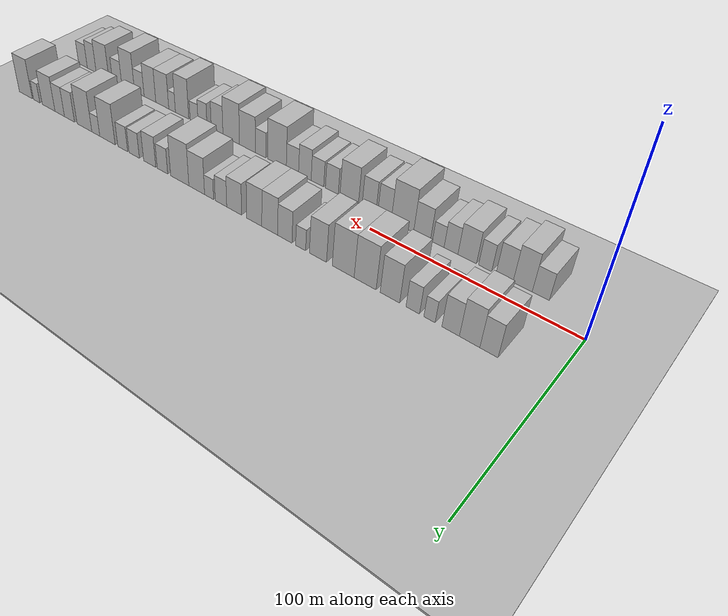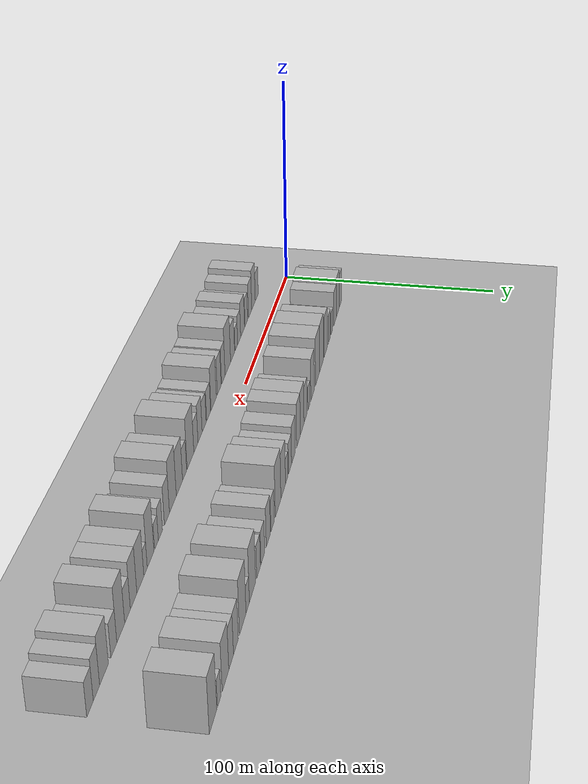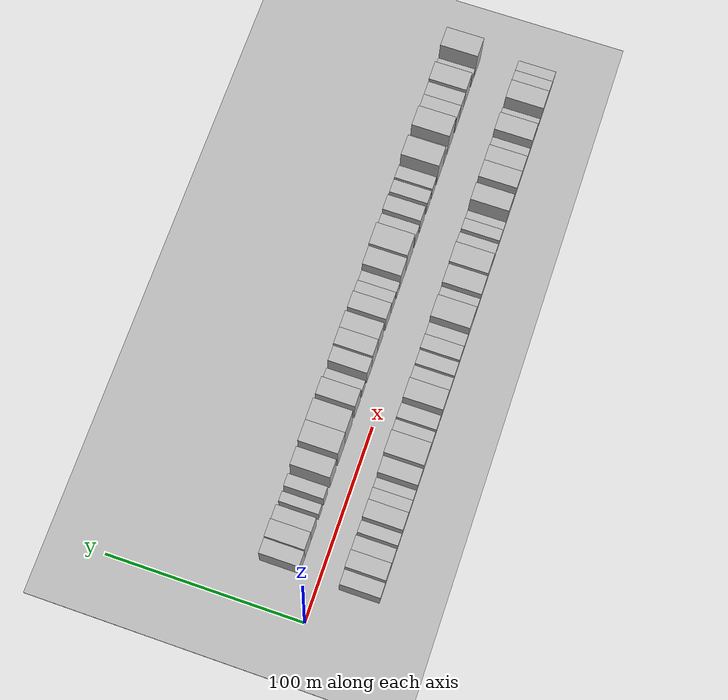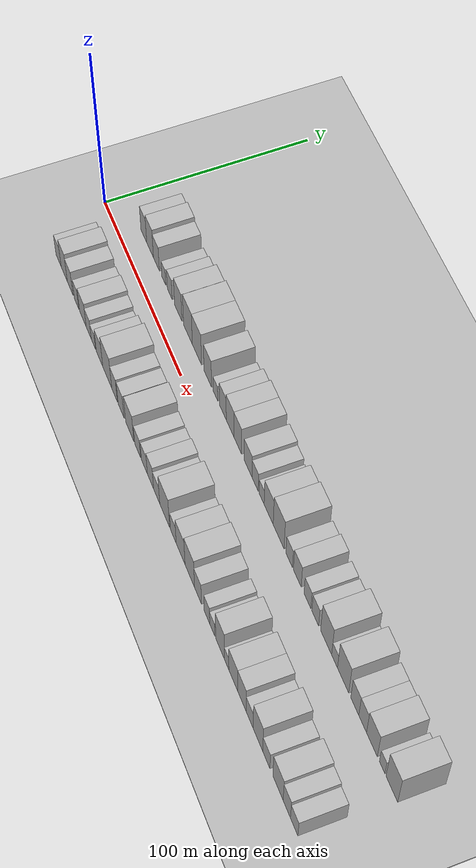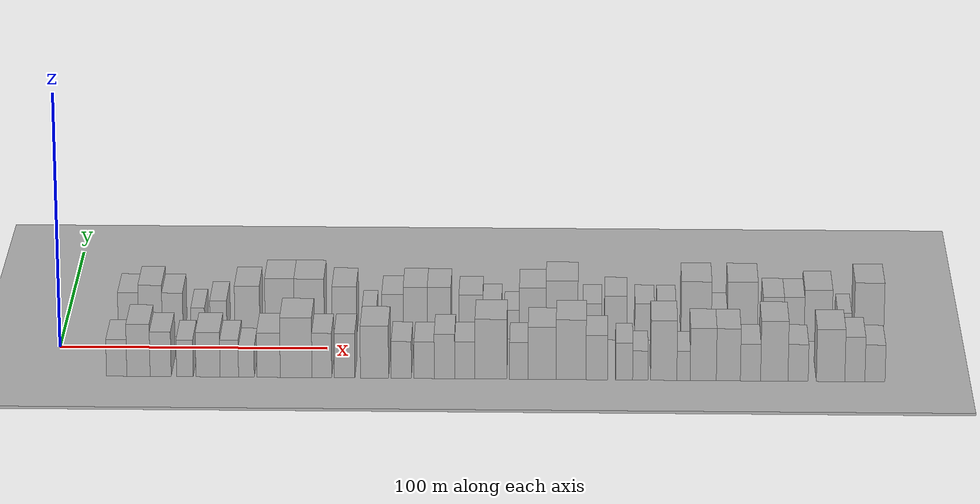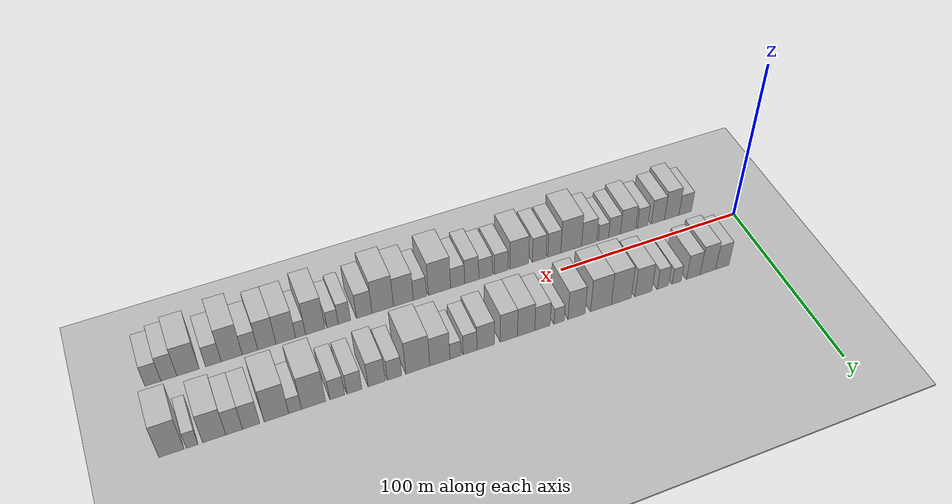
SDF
<?xml version="1.0" encoding="utf-8"?>

<sdf version="1.6">

   <world name="default">

      <gui fullscreen="0">

         <camera name="user_camera">

            <pose>-15 0 4.57585 0 0 0</pose>

            <view_controller>orbit</view_controller>

         </camera>

      </gui>

      <scene>

         <sky>

           <clouds>

             <speed>12</speed>

           </clouds>

         </sky>

         <ambient>0.4 0.4 0.4 1</ambient>

         <background>0.7 0.7 0.7 1</background>

         <shadows>1</shadows>

      </scene>

      <gravity>0 0 -9.8066</gravity>

      <magnetic_field>6e-06 2.3e-05 -4.2e-05</magnetic_field>

      <physics default="0" name="default_physics" type="ode">

         <ode>

            <solver>

               <type>quick</type>

               <iters>10</iters>

               <sor>1.0</sor>

               <use_dynamic_moi_rescaling>0</use_dynamic_moi_rescaling>

            </solver>

            <constraints>

               <cfm>0</cfm>

               <erp>0.2</erp>

               <contact_max_correcting_vel>100</contact_max_correcting_vel>

               <contact_surface_layer>0.001</contact_surface_layer>

            </constraints>

         </ode>

         <max_step_size>0.004</max_step_size>

         <real_time_factor>1</real_time_factor>

         <real_time_update_rate>250</real_time_update_rate>

      </physics>

      <light name="sun" type="directional">

         <cast_shadows>1</cast_shadows>

         <pose>0 0 10 0 0 0</pose>

         <diffuse>0.8 0.8 0.8 1</diffuse>

         <specular>0.2 0.2 0.2 1</specular>

         <attenuation>

            <range>1000</range>

            <constant>0.9</constant>

            <linear>0.01</linear>

            <quadratic>0.001</quadratic>

         </attenuation>

         <direction>-0.5 0.1 -0.9</direction>

      </light>

      <include>

         <name>ground_plane_1</name>

         <uri>model://HANNAS_ground_plane</uri>

         <pose>0 0 0  0 0 0</pose>

      </include>

      <include>

         <name>ground_plane_2</name>

         <uri>model://HANNAS_ground_plane</uri>

         <pose>100 0 0  0 0 0</pose>

      </include>

      <model name="building_1">

         <static>1</static>

         <pose frame="">24.8415 20.0000 0 0.000000 0.000000 1.570796</pose>

         <link name="link">

            <pose frame="">0 0 9.00 0 0 0</pose>

            <collision name="collision">

               <geometry>

                  <box>

                     <size>20.0000 7.6830 18.0000</size>

                  </box>

               </geometry>

               <max_contacts>10</max_contacts>

               <surface>

                  <contact>

                     <ode/>

                  </contact>

                  <bounce/>

                  <friction>

                     <torsional>

                        <ode/>

                     </torsional>

                     <ode/>

                  </friction>

               </surface>

            </collision>

            <visual name="visual">

               <cast_shadows>0</cast_shadows>

               <geometry>

                  <box>

                     <size>20.0000 7.6830 18.0000</size>

                  </box>

               </geometry>

               <material>

                  <script>

                     <uri>model://HANNAS_wall/materials/scripts</uri>

                     <uri>model://HANNAS_wall/materials/textures</uri>

                     <name>vrc/HANNAS_wall</name>

                  </script>

               </material>

            </visual>

            <self_collide>0</self_collide>

            <enable_wind>0</enable_wind>

            <kinematic>0</kinematic>

         </link>

      </model>

      <model name="building_2">

         <static>1</static>

         <pose frame="">33.1000 20.0000 0 0.000000 0.000000 1.570796</pose>

         <link name="link">

            <pose frame="">0 0 10.50 0 0 0</pose>

            <collision name="collision">

               <geometry>

                  <box>

                     <size>20.0000 8.8340 21.0000</size>

                  </box>

               </geometry>

               <max_contacts>10</max_contacts>

               <surface>

                  <contact>

                     <ode/>

                  </contact>

                  <bounce/>

                  <friction>

                     <torsional>

                        <ode/>

                     </torsional>

                     <ode/>

                  </friction>

               </surface>

            </collision>

            <visual name="visual">

               <cast_shadows>0</cast_shadows>

               <geometry>

                  <box>

                     <size>20.0000 8.8340 21.0000</size>

                  </box>

               </geometry>

               <material>

                  <script>

                     <uri>model://HANNAS_wall/materials/scripts</uri>

                     <uri>model://HANNAS_wall/materials/textures</uri>

                     <name>vrc/HANNAS_wall</name>

                  </script>

               </material>

            </visual>

            <self_collide>0</self_collide>

            <enable_wind>0</enable_wind>

            <kinematic>0</kinematic>

         </link>

      </model>

      <model name="building_3">

         <static>1</static>

         <pose frame="">41.4182 20.0000 0 0.000000 0.000000 1.570796</pose>

         <link name="link">

            <pose frame="">0 0 9.00 0 0 0</pose>

            <collision name="collision">

               <geometry>

                  <box>

                     <size>20.0000 7.8023 18.0000</size>

                  </box>

               </geometry>

               <max_contacts>10</max_contacts>

               <surface>

                  <contact>

                     <ode/>

                  </contact>

                  <bounce/>

                  <friction>

                     <torsional>

                        <ode/>

                     </torsional>

                     <ode/>

                  </friction>

               </surface>

            </collision>

            <visual name="visual">

               <cast_shadows>0</cast_shadows>

               <geometry>

                  <box>

                     <size>20.0000 7.8023 18.0000</size>

                  </box>

               </geometry>

               <material>

                  <script>

                     <uri>model://HANNAS_wall/materials/scripts</uri>

                     <uri>model://HANNAS_wall/materials/textures</uri>

                     <name>vrc/HANNAS_wall</name>

                  </script>

               </material>

            </visual>

            <self_collide>0</self_collide>

            <enable_wind>0</enable_wind>

            <kinematic>0</kinematic>

         </link>

      </model>

      <model name="building_4">

         <static>1</static>

         <pose frame="">50.8938 20.0000 0 0.000000 0.000000 1.570796</pose>

         <link name="link">

            <pose frame="">0 0 6.00 0 0 0</pose>

            <collision name="collision">

               <geometry>

                  <box>

                     <size>20.0000 5.1490 12.0000</size>

                  </box>

               </geometry>

               <max_contacts>10</max_contacts>

               <surface>

                  <contact>

                     <ode/>

                  </contact>

                  <bounce/>

                  <friction>

                     <torsional>

                        <ode/>

                     </torsional>

                     <ode/>

                  </friction>

               </surface>

            </collision>

            <visual name="visual">

               <cast_shadows>0</cast_shadows>

               <geometry>

                  <box>

                     <size>20.0000 5.1490 12.0000</size>

                  </box>

               </geometry>

               <material>

                  <script>

                     <uri>model://HANNAS_wall/materials/scripts</uri>

                     <uri>model://HANNAS_wall/materials/textures</uri>

                     <name>vrc/HANNAS_wall</name>

                  </script>

               </material>

            </visual>

            <self_collide>0</self_collide>

            <enable_wind>0</enable_wind>

            <kinematic>0</kinematic>

         </link>

      </model>

      <model name="building_5">

         <static>1</static>

         <pose frame="">58.6183 20.0000 0 0.000000 0.000000 1.570796</pose>

         <link name="link">

            <pose frame="">0 0 7.50 0 0 0</pose>

            <collision name="collision">

               <geometry>

                  <box>

                     <size>20.0000 6.2999 15.0000</size>

                  </box>

               </geometry>

               <max_contacts>10</max_contacts>

               <surface>

                  <contact>

                     <ode/>

                  </contact>

                  <bounce/>

                  <friction>

                     <torsional>

                        <ode/>

                     </torsional>

                     <ode/>

                  </friction>

               </surface>

            </collision>

            <visual name="visual">

               <cast_shadows>0</cast_shadows>

               <geometry>

                  <box>

                     <size>20.0000 6.2999 15.0000</size>

                  </box>

               </geometry>

               <material>

                  <script>

                     <uri>model://HANNAS_wall/materials/scripts</uri>

                     <uri>model://HANNAS_wall/materials/textures</uri>

                     <name>vrc/HANNAS_wall</name>

                  </script>

               </material>

            </visual>

            <self_collide>0</self_collide>

            <enable_wind>0</enable_wind>

            <kinematic>0</kinematic>

         </link>

      </model>

      <model name="building_6">

         <static>1</static>

         <pose frame="">69.4453 20.0000 0 0.000000 0.000000 1.570796</pose>

         <link name="link">

            <pose frame="">0 0 10.50 0 0 0</pose>

            <collision name="collision">

               <geometry>

                  <box>

                     <size>20.0000 9.3541 21.0000</size>

                  </box>

               </geometry>

               <max_contacts>10</max_contacts>

               <surface>

                  <contact>

                     <ode/>

                  </contact>

                  <bounce/>

                  <friction>

                     <torsional>

                        <ode/>

                     </torsional>

                     <ode/>

                  </friction>

               </surface>

            </collision>

            <visual name="visual">

               <cast_shadows>0</cast_shadows>

               <geometry>

                  <box>

                     <size>20.0000 9.3541 21.0000</size>

                  </box>

               </geometry>

               <material>

                  <script>

                     <uri>model://HANNAS_wall/materials/scripts</uri>

                     <uri>model://HANNAS_wall/materials/textures</uri>

                     <name>vrc/HANNAS_wall</name>

                  </script>

               </material>

            </visual>

            <self_collide>0</self_collide>

            <enable_wind>0</enable_wind>

            <kinematic>0</kinematic>

         </link>

      </model>

      <model name="building_7">

         <static>1</static>

         <pose frame="">81.5799 20.0000 0 0.000000 0.000000 1.570796</pose>

         <link name="link">

            <pose frame="">0 0 12.00 0 0 0</pose>

            <collision name="collision">

               <geometry>

                  <box>

                     <size>20.0000 10.9151 24.0000</size>

                  </box>

               </geometry>

               <max_contacts>10</max_contacts>

               <surface>

                  <contact>

                     <ode/>

                  </contact>

                  <bounce/>

                  <friction>

                     <torsional>

                        <ode/>

                     </torsional>

                     <ode/>

                  </friction>

               </surface>

            </collision>

            <visual name="visual">

               <cast_shadows>0</cast_shadows>

               <geometry>

                  <box>

                     <size>20.0000 10.9151 24.0000</size>

                  </box>

               </geometry>

               <material>

                  <script>

                     <uri>model://HANNAS_wall/materials/scripts</uri>

                     <uri>model://HANNAS_wall/materials/textures</uri>

                     <name>vrc/HANNAS_wall</name>

                  </script>

               </material>

            </visual>

            <self_collide>0</self_collide>

            <enable_wind>0</enable_wind>

            <kinematic>0</kinematic>

         </link>

      </model>

      <model name="building_8">

         <static>1</static>

         <pose frame="">92.6575 20.0000 0 0.000000 0.000000 1.570796</pose>

         <link name="link">

            <pose frame="">0 0 12.00 0 0 0</pose>

            <collision name="collision">

               <geometry>

                  <box>

                     <size>20.0000 11.2401 24.0000</size>

                  </box>

               </geometry>

               <max_contacts>10</max_contacts>

               <surface>

                  <contact>

                     <ode/>

                  </contact>

                  <bounce/>

                  <friction>

                     <torsional>

                        <ode/>

                     </torsional>

                     <ode/>

                  </friction>

               </surface>

            </collision>

            <visual name="visual">

               <cast_shadows>0</cast_shadows>

               <geometry>

                  <box>

                     <size>20.0000 11.2401 24.0000</size>

                  </box>

               </geometry>

               <material>

                  <script>

                     <uri>model://HANNAS_wall/materials/scripts</uri>

                     <uri>model://HANNAS_wall/materials/textures</uri>

                     <name>vrc/HANNAS_wall</name>

                  </script>

               </material>

            </visual>

            <self_collide>0</self_collide>

            <enable_wind>0</enable_wind>

            <kinematic>0</kinematic>

         </link>

      </model>

      <model name="building_9">

         <static>1</static>

         <pose frame="">105.8259 20.0000 0 0.000000 0.000000 1.570796</pose>

         <link name="link">

            <pose frame="">0 0 10.50 0 0 0</pose>

            <collision name="collision">

               <geometry>

                  <box>

                     <size>20.0000 9.0966 21.0000</size>

                  </box>

               </geometry>

               <max_contacts>10</max_contacts>

               <surface>

                  <contact>

                     <ode/>

                  </contact>

                  <bounce/>

                  <friction>

                     <torsional>

                        <ode/>

                     </torsional>

                     <ode/>

                  </friction>

               </surface>

            </collision>

            <visual name="visual">

               <cast_shadows>0</cast_shadows>

               <geometry>

                  <box>

                     <size>20.0000 9.0966 21.0000</size>

                  </box>

               </geometry>

               <material>

                  <script>

                     <uri>model://HANNAS_wall/materials/scripts</uri>

                     <uri>model://HANNAS_wall/materials/textures</uri>

                     <name>vrc/HANNAS_wall</name>

                  </script>

               </material>

            </visual>

            <self_collide>0</self_collide>

            <enable_wind>0</enable_wind>

            <kinematic>0</kinematic>

         </link>

      </model>

      <model name="building_10">

         <static>1</static>

         <pose frame="">115.0987 20.0000 0 0.000000 0.000000 1.570796</pose>

         <link name="link">

            <pose frame="">0 0 6.00 0 0 0</pose>

            <collision name="collision">

               <geometry>

                  <box>

                     <size>20.0000 5.4492 12.0000</size>

                  </box>

               </geometry>

               <max_contacts>10</max_contacts>

               <surface>

                  <contact>

                     <ode/>

                  </contact>

                  <bounce/>

                  <friction>

                     <torsional>

                        <ode/>

                     </torsional>

                     <ode/>

                  </friction>

               </surface>

            </collision>

            <visual name="visual">

               <cast_shadows>0</cast_shadows>

               <geometry>

                  <box>

                     <size>20.0000 5.4492 12.0000</size>

                  </box>

               </geometry>

               <material>

                  <script>

                     <uri>model://HANNAS_wall/materials/scripts</uri>

                     <uri>model://HANNAS_wall/materials/textures</uri>

                     <name>vrc/HANNAS_wall</name>

                  </script>

               </material>

            </visual>

            <self_collide>0</self_collide>

            <enable_wind>0</enable_wind>

            <kinematic>0</kinematic>

         </link>

      </model>

      <model name="building_11">

         <static>1</static>

         <pose frame="">123.8498 20.0000 0 0.000000 0.000000 1.570796</pose>

         <link name="link">

            <pose frame="">0 0 9.00 0 0 0</pose>

            <collision name="collision">

               <geometry>

                  <box>

                     <size>20.0000 8.0529 18.0000</size>

                  </box>

               </geometry>

               <max_contacts>10</max_contacts>

               <surface>

                  <contact>

                     <ode/>

                  </contact>

                  <bounce/>

                  <friction>

                     <torsional>

                        <ode/>

                     </torsional>

                     <ode/>

                  </friction>

               </surface>

            </collision>

            <visual name="visual">

               <cast_shadows>0</cast_shadows>

               <geometry>

                  <box>

                     <size>20.0000 8.0529 18.0000</size>

                  </box>

               </geometry>

               <material>

                  <script>

                     <uri>model://HANNAS_wall/materials/scripts</uri>

                     <uri>model://HANNAS_wall/materials/textures</uri>

                     <name>vrc/HANNAS_wall</name>

                  </script>

               </material>

            </visual>

            <self_collide>0</self_collide>

            <enable_wind>0</enable_wind>

            <kinematic>0</kinematic>

         </link>

      </model>

      <model name="building_12">

         <static>1</static>

         <pose frame="">132.3652 20.0000 0 0.000000 0.000000 1.570796</pose>

         <link name="link">

            <pose frame="">0 0 10.50 0 0 0</pose>

            <collision name="collision">

               <geometry>

                  <box>

                     <size>20.0000 8.9779 21.0000</size>

                  </box>

               </geometry>

               <max_contacts>10</max_contacts>

               <surface>

                  <contact>

                     <ode/>

                  </contact>

                  <bounce/>

                  <friction>

                     <torsional>

                        <ode/>

                     </torsional>

                     <ode/>

                  </friction>

               </surface>

            </collision>

            <visual name="visual">

               <cast_shadows>0</cast_shadows>

               <geometry>

                  <box>

                     <size>20.0000 8.9779 21.0000</size>

                  </box>

               </geometry>

               <material>

                  <script>

                     <uri>model://HANNAS_wall/materials/scripts</uri>

                     <uri>model://HANNAS_wall/materials/textures</uri>

                     <name>vrc/HANNAS_wall</name>

                  </script>

               </material>

            </visual>

            <self_collide>0</self_collide>

            <enable_wind>0</enable_wind>

            <kinematic>0</kinematic>

         </link>

      </model>

      <model name="building_13">

         <static>1</static>

         <pose frame="">141.2884 20.0000 0 0.000000 0.000000 1.570796</pose>

         <link name="link">

            <pose frame="">0 0 10.50 0 0 0</pose>

            <collision name="collision">

               <geometry>

                  <box>

                     <size>20.0000 8.8684 21.0000</size>

                  </box>

               </geometry>

               <max_contacts>10</max_contacts>

               <surface>

                  <contact>

                     <ode/>

                  </contact>

                  <bounce/>

                  <friction>

                     <torsional>

                        <ode/>

                     </torsional>

                     <ode/>

                  </friction>

               </surface>

            </collision>

            <visual name="visual">

               <cast_shadows>0</cast_shadows>

               <geometry>

                  <box>

                     <size>20.0000 8.8684 21.0000</size>

                  </box>

               </geometry>

               <material>

                  <script>

                     <uri>model://HANNAS_wall/materials/scripts</uri>

                     <uri>model://HANNAS_wall/materials/textures</uri>

                     <name>vrc/HANNAS_wall</name>

                  </script>

               </material>

            </visual>

            <self_collide>0</self_collide>

            <enable_wind>0</enable_wind>

            <kinematic>0</kinematic>

         </link>

      </model>

      <model name="building_14">

         <static>1</static>

         <pose frame="">153.1713 20.0000 0 0.000000 0.000000 1.570796</pose>

         <link name="link">

            <pose frame="">0 0 9.00 0 0 0</pose>

            <collision name="collision">

               <geometry>

                  <box>

                     <size>20.0000 8.8973 18.0000</size>

                  </box>

               </geometry>

               <max_contacts>10</max_contacts>

               <surface>

                  <contact>

                     <ode/>

                  </contact>

                  <bounce/>

                  <friction>

                     <torsional>

                        <ode/>

                     </torsional>

                     <ode/>

                  </friction>

               </surface>

            </collision>

            <visual name="visual">

               <cast_shadows>0</cast_shadows>

               <geometry>

                  <box>

                     <size>20.0000 8.8973 18.0000</size>

                  </box>

               </geometry>

               <material>

                  <script>

                     <uri>model://HANNAS_wall/materials/scripts</uri>

                     <uri>model://HANNAS_wall/materials/textures</uri>

                     <name>vrc/HANNAS_wall</name>

                  </script>

               </material>

            </visual>

            <self_collide>0</self_collide>

            <enable_wind>0</enable_wind>

            <kinematic>0</kinematic>

         </link>

      </model>

      <model name="building_15">

         <static>1</static>

         <pose frame="">161.1512 20.0000 0 0.000000 0.000000 1.570796</pose>

         <link name="link">

            <pose frame="">0 0 7.50 0 0 0</pose>

            <collision name="collision">

               <geometry>

                  <box>

                     <size>20.0000 7.0626 15.0000</size>

                  </box>

               </geometry>

               <max_contacts>10</max_contacts>

               <surface>

                  <contact>

                     <ode/>

                  </contact>

                  <bounce/>

                  <friction>

                     <torsional>

                        <ode/>

                     </torsional>

                     <ode/>

                  </friction>

               </surface>

            </collision>

            <visual name="visual">

               <cast_shadows>0</cast_shadows>

               <geometry>

                  <box>

                     <size>20.0000 7.0626 15.0000</size>

                  </box>

               </geometry>

               <material>

                  <script>

                     <uri>model://HANNAS_wall/materials/scripts</uri>

                     <uri>model://HANNAS_wall/materials/textures</uri>

                     <name>vrc/HANNAS_wall</name>

                  </script>

               </material>

            </visual>

            <self_collide>0</self_collide>

            <enable_wind>0</enable_wind>

            <kinematic>0</kinematic>

         </link>

      </model>

      <model name="building_16">

         <static>1</static>

         <pose frame="">168.5036 20.0000 0 0.000000 0.000000 1.570796</pose>

         <link name="link">

            <pose frame="">0 0 6.00 0 0 0</pose>

            <collision name="collision">

               <geometry>

                  <box>

                     <size>20.0000 5.6421 12.0000</size>

                  </box>

               </geometry>

               <max_contacts>10</max_contacts>

               <surface>

                  <contact>

                     <ode/>

                  </contact>

                  <bounce/>

                  <friction>

                     <torsional>

                        <ode/>

                     </torsional>

                     <ode/>

                  </friction>

               </surface>

            </collision>

            <visual name="visual">

               <cast_shadows>0</cast_shadows>

               <geometry>

                  <box>

                     <size>20.0000 5.6421 12.0000</size>

                  </box>

               </geometry>

               <material>

                  <script>

                     <uri>model://HANNAS_wall/materials/scripts</uri>

                     <uri>model://HANNAS_wall/materials/textures</uri>

                     <name>vrc/HANNAS_wall</name>

                  </script>

               </material>

            </visual>

            <self_collide>0</self_collide>

            <enable_wind>0</enable_wind>

            <kinematic>0</kinematic>

         </link>

      </model>

      <model name="building_17">

         <static>1</static>

         <pose frame="">176.3258 20.0000 0 0.000000 0.000000 1.570796</pose>

         <link name="link">

            <pose frame="">0 0 10.50 0 0 0</pose>

            <collision name="collision">

               <geometry>

                  <box>

                     <size>20.0000 10.0022 21.0000</size>

                  </box>

               </geometry>

               <max_contacts>10</max_contacts>

               <surface>

                  <contact>

                     <ode/>

                  </contact>

                  <bounce/>

                  <friction>

                     <torsional>

                        <ode/>

                     </torsional>

                     <ode/>

                  </friction>

               </surface>

            </collision>

            <visual name="visual">

               <cast_shadows>0</cast_shadows>

               <geometry>

                  <box>

                     <size>20.0000 10.0022 21.0000</size>

                  </box>

               </geometry>

               <material>

                  <script>

                     <uri>model://HANNAS_wall/materials/scripts</uri>

                     <uri>model://HANNAS_wall/materials/textures</uri>

                     <name>vrc/HANNAS_wall</name>

                  </script>

               </material>

            </visual>

            <self_collide>0</self_collide>

            <enable_wind>0</enable_wind>

            <kinematic>0</kinematic>

         </link>

      </model>

      <model name="building_18">

         <static>1</static>

         <pose frame="">187.2742 20.0000 0 0.000000 0.000000 1.570796</pose>

         <link name="link">

            <pose frame="">0 0 12.00 0 0 0</pose>

            <collision name="collision">

               <geometry>

                  <box>

                     <size>20.0000 11.8946 24.0000</size>

                  </box>

               </geometry>

               <max_contacts>10</max_contacts>

               <surface>

                  <contact>

                     <ode/>

                  </contact>

                  <bounce/>

                  <friction>

                     <torsional>

                        <ode/>

                     </torsional>

                     <ode/>

                  </friction>

               </surface>

            </collision>

            <visual name="visual">

               <cast_shadows>0</cast_shadows>

               <geometry>

                  <box>

                     <size>20.0000 11.8946 24.0000</size>

                  </box>

               </geometry>

               <material>

                  <script>

                     <uri>model://HANNAS_wall/materials/scripts</uri>

                     <uri>model://HANNAS_wall/materials/textures</uri>

                     <name>vrc/HANNAS_wall</name>

                  </script>

               </material>

            </visual>

            <self_collide>0</self_collide>

            <enable_wind>0</enable_wind>

            <kinematic>0</kinematic>

         </link>

      </model>

      <model name="building_19">

         <static>1</static>

         <pose frame="">198.7314 20.0000 0 0.000000 0.000000 1.570796</pose>

         <link name="link">

            <pose frame="">0 0 7.50 0 0 0</pose>

            <collision name="collision">

               <geometry>

                  <box>

                     <size>20.0000 7.0198 15.0000</size>

                  </box>

               </geometry>

               <max_contacts>10</max_contacts>

               <surface>

                  <contact>

                     <ode/>

                  </contact>

                  <bounce/>

                  <friction>

                     <torsional>

                        <ode/>

                     </torsional>

                     <ode/>

                  </friction>

               </surface>

            </collision>

            <visual name="visual">

               <cast_shadows>0</cast_shadows>

               <geometry>

                  <box>

                     <size>20.0000 7.0198 15.0000</size>

                  </box>

               </geometry>

               <material>

                  <script>

                     <uri>model://HANNAS_wall/materials/scripts</uri>

                     <uri>model://HANNAS_wall/materials/textures</uri>

                     <name>vrc/HANNAS_wall</name>

                  </script>

               </material>

            </visual>

            <self_collide>0</self_collide>

            <enable_wind>0</enable_wind>

            <kinematic>0</kinematic>

         </link>

      </model>

      <model name="building_20">

         <static>1</static>

         <pose frame="">207.4007 20.0000 0 0.000000 0.000000 1.570796</pose>

         <link name="link">

            <pose frame="">0 0 9.00 0 0 0</pose>

            <collision name="collision">

               <geometry>

                  <box>

                     <size>20.0000 8.3186 18.0000</size>

                  </box>

               </geometry>

               <max_contacts>10</max_contacts>

               <surface>

                  <contact>

                     <ode/>

                  </contact>

                  <bounce/>

                  <friction>

                     <torsional>

                        <ode/>

                     </torsional>

                     <ode/>

                  </friction>

               </surface>

            </collision>

            <visual name="visual">

               <cast_shadows>0</cast_shadows>

               <geometry>

                  <box>

                     <size>20.0000 8.3186 18.0000</size>

                  </box>

               </geometry>

               <material>

                  <script>

                     <uri>model://HANNAS_wall/materials/scripts</uri>

                     <uri>model://HANNAS_wall/materials/textures</uri>

                     <name>vrc/HANNAS_wall</name>

                  </script>

               </material>

            </visual>

            <self_collide>0</self_collide>

            <enable_wind>0</enable_wind>

            <kinematic>0</kinematic>

         </link>

      </model>

      <model name="building_21">

         <static>1</static>

         <pose frame="">218.1752 20.0000 0 0.000000 0.000000 1.570796</pose>

         <link name="link">

            <pose frame="">0 0 7.50 0 0 0</pose>

            <collision name="collision">

               <geometry>

                  <box>

                     <size>20.0000 7.2304 15.0000</size>

                  </box>

               </geometry>

               <max_contacts>10</max_contacts>

               <surface>

                  <contact>

                     <ode/>

                  </contact>

                  <bounce/>

                  <friction>

                     <torsional>

                        <ode/>

                     </torsional>

                     <ode/>

                  </friction>

               </surface>

            </collision>

            <visual name="visual">

               <cast_shadows>0</cast_shadows>

               <geometry>

                  <box>

                     <size>20.0000 7.2304 15.0000</size>

                  </box>

               </geometry>

               <material>

                  <script>

                     <uri>model://HANNAS_wall/materials/scripts</uri>

                     <uri>model://HANNAS_wall/materials/textures</uri>

                     <name>vrc/HANNAS_wall</name>

                  </script>

               </material>

            </visual>

            <self_collide>0</self_collide>

            <enable_wind>0</enable_wind>

            <kinematic>0</kinematic>

         </link>

      </model>

      <model name="building_22">

         <static>1</static>

         <pose frame="">226.3134 20.0000 0 0.000000 0.000000 1.570796</pose>

         <link name="link">

            <pose frame="">0 0 7.50 0 0 0</pose>

            <collision name="collision">

               <geometry>

                  <box>

                     <size>20.0000 7.0461 15.0000</size>

                  </box>

               </geometry>

               <max_contacts>10</max_contacts>

               <surface>

                  <contact>

                     <ode/>

                  </contact>

                  <bounce/>

                  <friction>

                     <torsional>

                        <ode/>

                     </torsional>

                     <ode/>

                  </friction>

               </surface>

            </collision>

            <visual name="visual">

               <cast_shadows>0</cast_shadows>

               <geometry>

                  <box>

                     <size>20.0000 7.0461 15.0000</size>

                  </box>

               </geometry>

               <material>

                  <script>

                     <uri>model://HANNAS_wall/materials/scripts</uri>

                     <uri>model://HANNAS_wall/materials/textures</uri>

                     <name>vrc/HANNAS_wall</name>

                  </script>

               </material>

            </visual>

            <self_collide>0</self_collide>

            <enable_wind>0</enable_wind>

            <kinematic>0</kinematic>

         </link>

      </model>

      <model name="building_23">

         <static>1</static>

         <pose frame="">237.4874 20.0000 0 0.000000 0.000000 1.570796</pose>

         <link name="link">

            <pose frame="">0 0 12.00 0 0 0</pose>

            <collision name="collision">

               <geometry>

                  <box>

                     <size>20.0000 11.3018 24.0000</size>

                  </box>

               </geometry>

               <max_contacts>10</max_contacts>

               <surface>

                  <contact>

                     <ode/>

                  </contact>

                  <bounce/>

                  <friction>

                     <torsional>

                        <ode/>

                     </torsional>

                     <ode/>

                  </friction>

               </surface>

            </collision>

            <visual name="visual">

               <cast_shadows>0</cast_shadows>

               <geometry>

                  <box>

                     <size>20.0000 11.3018 24.0000</size>

                  </box>

               </geometry>

               <material>

                  <script>

                     <uri>model://HANNAS_wall/materials/scripts</uri>

                     <uri>model://HANNAS_wall/materials/textures</uri>

                     <name>vrc/HANNAS_wall</name>

                  </script>

               </material>

            </visual>

            <self_collide>0</self_collide>

            <enable_wind>0</enable_wind>

            <kinematic>0</kinematic>

         </link>

      </model>

      <model name="building_24">

         <static>1</static>

         <pose frame="">246.1157 20.0000 0 0.000000 0.000000 1.570796</pose>

         <link name="link">

            <pose frame="">0 0 6.00 0 0 0</pose>

            <collision name="collision">

               <geometry>

                  <box>

                     <size>20.0000 5.9548 12.0000</size>

                  </box>

               </geometry>

               <max_contacts>10</max_contacts>

               <surface>

                  <contact>

                     <ode/>

                  </contact>

                  <bounce/>

                  <friction>

                     <torsional>

                        <ode/>

                     </torsional>

                     <ode/>

                  </friction>

               </surface>

            </collision>

            <visual name="visual">

               <cast_shadows>0</cast_shadows>

               <geometry>

                  <box>

                     <size>20.0000 5.9548 12.0000</size>

                  </box>

               </geometry>

               <material>

                  <script>

                     <uri>model://HANNAS_wall/materials/scripts</uri>

                     <uri>model://HANNAS_wall/materials/textures</uri>

                     <name>vrc/HANNAS_wall</name>

                  </script>

               </material>

            </visual>

            <self_collide>0</self_collide>

            <enable_wind>0</enable_wind>

            <kinematic>0</kinematic>

         </link>

      </model>

      <model name="building_25">

         <static>1</static>

         <pose frame="">254.7373 20.0000 0 0.000000 0.000000 1.570796</pose>

         <link name="link">

            <pose frame="">0 0 12.00 0 0 0</pose>

            <collision name="collision">

               <geometry>

                  <box>

                     <size>20.0000 11.2885 24.0000</size>

                  </box>

               </geometry>

               <max_contacts>10</max_contacts>

               <surface>

                  <contact>

                     <ode/>

                  </contact>

                  <bounce/>

                  <friction>

                     <torsional>

                        <ode/>

                     </torsional>

                     <ode/>

                  </friction>

               </surface>

            </collision>

            <visual name="visual">

               <cast_shadows>0</cast_shadows>

               <geometry>

                  <box>

                     <size>20.0000 11.2885 24.0000</size>

                  </box>

               </geometry>

               <material>

                  <script>

                     <uri>model://HANNAS_wall/materials/scripts</uri>

                     <uri>model://HANNAS_wall/materials/textures</uri>

                     <name>vrc/HANNAS_wall</name>

                  </script>

               </material>

            </visual>

            <self_collide>0</self_collide>

            <enable_wind>0</enable_wind>

            <kinematic>0</kinematic>

         </link>

      </model>

      <model name="building_26">

         <static>1</static>

         <pose frame="">266.3388 20.0000 0 0.000000 0.000000 1.570796</pose>

         <link name="link">

            <pose frame="">0 0 9.00 0 0 0</pose>

            <collision name="collision">

               <geometry>

                  <box>

                     <size>20.0000 7.9144 18.0000</size>

                  </box>

               </geometry>

               <max_contacts>10</max_contacts>

               <surface>

                  <contact>

                     <ode/>

                  </contact>

                  <bounce/>

                  <friction>

                     <torsional>

                        <ode/>

                     </torsional>

                     <ode/>

                  </friction>

               </surface>

            </collision>

            <visual name="visual">

               <cast_shadows>0</cast_shadows>

               <geometry>

                  <box>

                     <size>20.0000 7.9144 18.0000</size>

                  </box>

               </geometry>

               <material>

                  <script>

                     <uri>model://HANNAS_wall/materials/scripts</uri>

                     <uri>model://HANNAS_wall/materials/textures</uri>

                     <name>vrc/HANNAS_wall</name>

                  </script>

               </material>

            </visual>

            <self_collide>0</self_collide>

            <enable_wind>0</enable_wind>

            <kinematic>0</kinematic>

         </link>

      </model>

      <model name="building_27">

         <static>1</static>

         <pose frame="">274.0850 20.0000 0 0.000000 0.000000 1.570796</pose>

         <link name="link">

            <pose frame="">0 0 9.00 0 0 0</pose>

            <collision name="collision">

               <geometry>

                  <box>

                     <size>20.0000 7.5781 18.0000</size>

                  </box>

               </geometry>

               <max_contacts>10</max_contacts>

               <surface>

                  <contact>

                     <ode/>

                  </contact>

                  <bounce/>

                  <friction>

                     <torsional>

                        <ode/>

                     </torsional>

                     <ode/>

                  </friction>

               </surface>

            </collision>

            <visual name="visual">

               <cast_shadows>0</cast_shadows>

               <geometry>

                  <box>

                     <size>20.0000 7.5781 18.0000</size>

                  </box>

               </geometry>

               <material>

                  <script>

                     <uri>model://HANNAS_wall/materials/scripts</uri>

                     <uri>model://HANNAS_wall/materials/textures</uri>

                     <name>vrc/HANNAS_wall</name>

                  </script>

               </material>

            </visual>

            <self_collide>0</self_collide>

            <enable_wind>0</enable_wind>

            <kinematic>0</kinematic>

         </link>

      </model>

      <model name="building_28">

         <static>1</static>

         <pose frame="">283.0653 20.0000 0 0.000000 0.000000 1.570796</pose>

         <link name="link">

            <pose frame="">0 0 10.50 0 0 0</pose>

            <collision name="collision">

               <geometry>

                  <box>

                     <size>20.0000 10.3824 21.0000</size>

                  </box>

               </geometry>

               <max_contacts>10</max_contacts>

               <surface>

                  <contact>

                     <ode/>

                  </contact>

                  <bounce/>

                  <friction>

                     <torsional>

                        <ode/>

                     </torsional>

                     <ode/>

                  </friction>

               </surface>

            </collision>

            <visual name="visual">

               <cast_shadows>0</cast_shadows>

               <geometry>

                  <box>

                     <size>20.0000 10.3824 21.0000</size>

                  </box>

               </geometry>

               <material>

                  <script>

                     <uri>model://HANNAS_wall/materials/scripts</uri>

                     <uri>model://HANNAS_wall/materials/textures</uri>

                     <name>vrc/HANNAS_wall</name>

                  </script>

               </material>

            </visual>

            <self_collide>0</self_collide>

            <enable_wind>0</enable_wind>

            <kinematic>0</kinematic>

         </link>

      </model>

      <model name="building_29">

         <static>1</static>

         <pose frame="">292.8766 20.0000 0 0.000000 0.000000 1.570796</pose>

         <link name="link">

            <pose frame="">0 0 6.00 0 0 0</pose>

            <collision name="collision">

               <geometry>

                  <box>

                     <size>20.0000 5.2401 12.0000</size>

                  </box>

               </geometry>

               <max_contacts>10</max_contacts>

               <surface>

                  <contact>

                     <ode/>

                  </contact>

                  <bounce/>

                  <friction>

                     <torsional>

                        <ode/>

                     </torsional>

                     <ode/>

                  </friction>

               </surface>

            </collision>

            <visual name="visual">

               <cast_shadows>0</cast_shadows>

               <geometry>

                  <box>

                     <size>20.0000 5.2401 12.0000</size>

                  </box>

               </geometry>

               <material>

                  <script>

                     <uri>model://HANNAS_wall/materials/scripts</uri>

                     <uri>model://HANNAS_wall/materials/textures</uri>

                     <name>vrc/HANNAS_wall</name>

                  </script>

               </material>

            </visual>

            <self_collide>0</self_collide>

            <enable_wind>0</enable_wind>

            <kinematic>0</kinematic>

         </link>

      </model>

      <model name="building_30">

         <static>1</static>

         <pose frame="">302.0170 20.0000 0 0.000000 0.000000 1.570796</pose>

         <link name="link">

            <pose frame="">0 0 12.00 0 0 0</pose>

            <collision name="collision">

               <geometry>

                  <box>

                     <size>20.0000 11.0407 24.0000</size>

                  </box>

               </geometry>

               <max_contacts>10</max_contacts>

               <surface>

                  <contact>

                     <ode/>

                  </contact>

                  <bounce/>

                  <friction>

                     <torsional>

                        <ode/>

                     </torsional>

                     <ode/>

                  </friction>

               </surface>

            </collision>

            <visual name="visual">

               <cast_shadows>0</cast_shadows>

               <geometry>

                  <box>

                     <size>20.0000 11.0407 24.0000</size>

                  </box>

               </geometry>

               <material>

                  <script>

                     <uri>model://HANNAS_wall/materials/scripts</uri>

                     <uri>model://HANNAS_wall/materials/textures</uri>

                     <name>vrc/HANNAS_wall</name>

                  </script>

               </material>

            </visual>

            <self_collide>0</self_collide>

            <enable_wind>0</enable_wind>

            <kinematic>0</kinematic>

         </link>

      </model>

      <model name="building_31">

         <static>1</static>

         <pose frame="">23.7424 -20.0000 0 0.000000 0.000000 1.570796</pose>

         <link name="link">

            <pose frame="">0 0 7.50 0 0 0</pose>

            <collision name="collision">

               <geometry>

                  <box>

                     <size>20.0000 7.4848 15.0000</size>

                  </box>

               </geometry>

               <max_contacts>10</max_contacts>

               <surface>

                  <contact>

                     <ode/>

                  </contact>

                  <bounce/>

                  <friction>

                     <torsional>

                        <ode/>

                     </torsional>

                     <ode/>

                  </friction>

               </surface>

            </collision>

            <visual name="visual">

               <cast_shadows>0</cast_shadows>

               <geometry>

                  <box>

                     <size>20.0000 7.4848 15.0000</size>

                  </box>

               </geometry>

               <material>

                  <script>

                     <uri>model://HANNAS_wall/materials/scripts</uri>

                     <uri>model://HANNAS_wall/materials/textures</uri>

                     <name>vrc/HANNAS_wall</name>

                  </script>

               </material>

            </visual>

            <self_collide>0</self_collide>

            <enable_wind>0</enable_wind>

            <kinematic>0</kinematic>

         </link>

      </model>

      <model name="building_32">

         <static>1</static>

         <pose frame="">31.7715 -20.0000 0 0.000000 0.000000 1.570796</pose>

         <link name="link">

            <pose frame="">0 0 10.50 0 0 0</pose>

            <collision name="collision">

               <geometry>

                  <box>

                     <size>20.0000 8.5735 21.0000</size>

                  </box>

               </geometry>

               <max_contacts>10</max_contacts>

               <surface>

                  <contact>

                     <ode/>

                  </contact>

                  <bounce/>

                  <friction>

                     <torsional>

                        <ode/>

                     </torsional>

                     <ode/>

                  </friction>

               </surface>

            </collision>

            <visual name="visual">

               <cast_shadows>0</cast_shadows>

               <geometry>

                  <box>

                     <size>20.0000 8.5735 21.0000</size>

                  </box>

               </geometry>

               <material>

                  <script>

                     <uri>model://HANNAS_wall/materials/scripts</uri>

                     <uri>model://HANNAS_wall/materials/textures</uri>

                     <name>vrc/HANNAS_wall</name>

                  </script>

               </material>

            </visual>

            <self_collide>0</self_collide>

            <enable_wind>0</enable_wind>

            <kinematic>0</kinematic>

         </link>

      </model>

      <model name="building_33">

         <static>1</static>

         <pose frame="">39.9363 -20.0000 0 0.000000 0.000000 1.570796</pose>

         <link name="link">

            <pose frame="">0 0 9.00 0 0 0</pose>

            <collision name="collision">

               <geometry>

                  <box>

                     <size>20.0000 7.7562 18.0000</size>

                  </box>

               </geometry>

               <max_contacts>10</max_contacts>

               <surface>

                  <contact>

                     <ode/>

                  </contact>

                  <bounce/>

                  <friction>

                     <torsional>

                        <ode/>

                     </torsional>

                     <ode/>

                  </friction>

               </surface>

            </collision>

            <visual name="visual">

               <cast_shadows>0</cast_shadows>

               <geometry>

                  <box>

                     <size>20.0000 7.7562 18.0000</size>

                  </box>

               </geometry>

               <material>

                  <script>

                     <uri>model://HANNAS_wall/materials/scripts</uri>

                     <uri>model://HANNAS_wall/materials/textures</uri>

                     <name>vrc/HANNAS_wall</name>

                  </script>

               </material>

            </visual>

            <self_collide>0</self_collide>

            <enable_wind>0</enable_wind>

            <kinematic>0</kinematic>

         </link>

      </model>

      <model name="building_34">

         <static>1</static>

         <pose frame="">48.8727 -20.0000 0 0.000000 0.000000 1.570796</pose>

         <link name="link">

            <pose frame="">0 0 7.50 0 0 0</pose>

            <collision name="collision">

               <geometry>

                  <box>

                     <size>20.0000 6.1164 15.0000</size>

                  </box>

               </geometry>

               <max_contacts>10</max_contacts>

               <surface>

                  <contact>

                     <ode/>

                  </contact>

                  <bounce/>

                  <friction>

                     <torsional>

                        <ode/>

                     </torsional>

                     <ode/>

                  </friction>

               </surface>

            </collision>

            <visual name="visual">

               <cast_shadows>0</cast_shadows>

               <geometry>

                  <box>

                     <size>20.0000 6.1164 15.0000</size>

                  </box>

               </geometry>

               <material>

                  <script>

                     <uri>model://HANNAS_wall/materials/scripts</uri>

                     <uri>model://HANNAS_wall/materials/textures</uri>

                     <name>vrc/HANNAS_wall</name>

                  </script>

               </material>

            </visual>

            <self_collide>0</self_collide>

            <enable_wind>0</enable_wind>

            <kinematic>0</kinematic>

         </link>

      </model>

      <model name="building_35">

         <static>1</static>

         <pose frame="">57.3761 -20.0000 0 0.000000 0.000000 1.570796</pose>

         <link name="link">

            <pose frame="">0 0 9.00 0 0 0</pose>

            <collision name="collision">

               <geometry>

                  <box>

                     <size>20.0000 8.8905 18.0000</size>

                  </box>

               </geometry>

               <max_contacts>10</max_contacts>

               <surface>

                  <contact>

                     <ode/>

                  </contact>

                  <bounce/>

                  <friction>

                     <torsional>

                        <ode/>

                     </torsional>

                     <ode/>

                  </friction>

               </surface>

            </collision>

            <visual name="visual">

               <cast_shadows>0</cast_shadows>

               <geometry>

                  <box>

                     <size>20.0000 8.8905 18.0000</size>

                  </box>

               </geometry>

               <material>

                  <script>

                     <uri>model://HANNAS_wall/materials/scripts</uri>

                     <uri>model://HANNAS_wall/materials/textures</uri>

                     <name>vrc/HANNAS_wall</name>

                  </script>

               </material>

            </visual>

            <self_collide>0</self_collide>

            <enable_wind>0</enable_wind>

            <kinematic>0</kinematic>

         </link>

      </model>

      <model name="building_36">

         <static>1</static>

         <pose frame="">65.2077 -20.0000 0 0.000000 0.000000 1.570796</pose>

         <link name="link">

            <pose frame="">0 0 7.50 0 0 0</pose>

            <collision name="collision">

               <geometry>

                  <box>

                     <size>20.0000 6.7727 15.0000</size>

                  </box>

               </geometry>

               <max_contacts>10</max_contacts>

               <surface>

                  <contact>

                     <ode/>

                  </contact>

                  <bounce/>

                  <friction>

                     <torsional>

                        <ode/>

                     </torsional>

                     <ode/>

                  </friction>

               </surface>

            </collision>

            <visual name="visual">

               <cast_shadows>0</cast_shadows>

               <geometry>

                  <box>

                     <size>20.0000 6.7727 15.0000</size>

                  </box>

               </geometry>

               <material>

                  <script>

                     <uri>model://HANNAS_wall/materials/scripts</uri>

                     <uri>model://HANNAS_wall/materials/textures</uri>

                     <name>vrc/HANNAS_wall</name>

                  </script>

               </material>

            </visual>

            <self_collide>0</self_collide>

            <enable_wind>0</enable_wind>

            <kinematic>0</kinematic>

         </link>

      </model>

      <model name="building_37">

         <static>1</static>

         <pose frame="">71.4955 -20.0000 0 0.000000 0.000000 1.570796</pose>

         <link name="link">

            <pose frame="">0 0 6.00 0 0 0</pose>

            <collision name="collision">

               <geometry>

                  <box>

                     <size>20.0000 5.8029 12.0000</size>

                  </box>

               </geometry>

               <max_contacts>10</max_contacts>

               <surface>

                  <contact>

                     <ode/>

                  </contact>

                  <bounce/>

                  <friction>

                     <torsional>

                        <ode/>

                     </torsional>

                     <ode/>

                  </friction>

               </surface>

            </collision>

            <visual name="visual">

               <cast_shadows>0</cast_shadows>

               <geometry>

                  <box>

                     <size>20.0000 5.8029 12.0000</size>

                  </box>

               </geometry>

               <material>

                  <script>

                     <uri>model://HANNAS_wall/materials/scripts</uri>

                     <uri>model://HANNAS_wall/materials/textures</uri>

                     <name>vrc/HANNAS_wall</name>

                  </script>

               </material>

            </visual>

            <self_collide>0</self_collide>

            <enable_wind>0</enable_wind>

            <kinematic>0</kinematic>

         </link>

      </model>

      <model name="building_38">

         <static>1</static>

         <pose frame="">79.6754 -20.0000 0 0.000000 0.000000 1.570796</pose>

         <link name="link">

            <pose frame="">0 0 9.00 0 0 0</pose>

            <collision name="collision">

               <geometry>

                  <box>

                     <size>20.0000 8.5568 18.0000</size>

                  </box>

               </geometry>

               <max_contacts>10</max_contacts>

               <surface>

                  <contact>

                     <ode/>

                  </contact>

                  <bounce/>

                  <friction>

                     <torsional>

                        <ode/>

                     </torsional>

                     <ode/>

                  </friction>

               </surface>

            </collision>

            <visual name="visual">

               <cast_shadows>0</cast_shadows>

               <geometry>

                  <box>

                     <size>20.0000 8.5568 18.0000</size>

                  </box>

               </geometry>

               <material>

                  <script>

                     <uri>model://HANNAS_wall/materials/scripts</uri>

                     <uri>model://HANNAS_wall/materials/textures</uri>

                     <name>vrc/HANNAS_wall</name>

                  </script>

               </material>

            </visual>

            <self_collide>0</self_collide>

            <enable_wind>0</enable_wind>

            <kinematic>0</kinematic>

         </link>

      </model>

      <model name="building_39">

         <static>1</static>

         <pose frame="">89.7910 -20.0000 0 0.000000 0.000000 1.570796</pose>

         <link name="link">

            <pose frame="">0 0 12.00 0 0 0</pose>

            <collision name="collision">

               <geometry>

                  <box>

                     <size>20.0000 11.6744 24.0000</size>

                  </box>

               </geometry>

               <max_contacts>10</max_contacts>

               <surface>

                  <contact>

                     <ode/>

                  </contact>

                  <bounce/>

                  <friction>

                     <torsional>

                        <ode/>

                     </torsional>

                     <ode/>

                  </friction>

               </surface>

            </collision>

            <visual name="visual">

               <cast_shadows>0</cast_shadows>

               <geometry>

                  <box>

                     <size>20.0000 11.6744 24.0000</size>

                  </box>

               </geometry>

               <material>

                  <script>

                     <uri>model://HANNAS_wall/materials/scripts</uri>

                     <uri>model://HANNAS_wall/materials/textures</uri>

                     <name>vrc/HANNAS_wall</name>

                  </script>

               </material>

            </visual>

            <self_collide>0</self_collide>

            <enable_wind>0</enable_wind>

            <kinematic>0</kinematic>

         </link>

      </model>

      <model name="building_40">

         <static>1</static>

         <pose frame="">99.2472 -20.0000 0 0.000000 0.000000 1.570796</pose>

         <link name="link">

            <pose frame="">0 0 9.00 0 0 0</pose>

            <collision name="collision">

               <geometry>

                  <box>

                     <size>20.0000 7.2381 18.0000</size>

                  </box>

               </geometry>

               <max_contacts>10</max_contacts>

               <surface>

                  <contact>

                     <ode/>

                  </contact>

                  <bounce/>

                  <friction>

                     <torsional>

                        <ode/>

                     </torsional>

                     <ode/>

                  </friction>

               </surface>

            </collision>

            <visual name="visual">

               <cast_shadows>0</cast_shadows>

               <geometry>

                  <box>

                     <size>20.0000 7.2381 18.0000</size>

                  </box>

               </geometry>

               <material>

                  <script>

                     <uri>model://HANNAS_wall/materials/scripts</uri>

                     <uri>model://HANNAS_wall/materials/textures</uri>

                     <name>vrc/HANNAS_wall</name>

                  </script>

               </material>

            </visual>

            <self_collide>0</self_collide>

            <enable_wind>0</enable_wind>

            <kinematic>0</kinematic>

         </link>

      </model>

      <model name="building_41">

         <static>1</static>

         <pose frame="">107.6433 -20.0000 0 0.000000 0.000000 1.570796</pose>

         <link name="link">

            <pose frame="">0 0 9.00 0 0 0</pose>

            <collision name="collision">

               <geometry>

                  <box>

                     <size>20.0000 7.5541 18.0000</size>

                  </box>

               </geometry>

               <max_contacts>10</max_contacts>

               <surface>

                  <contact>

                     <ode/>

                  </contact>

                  <bounce/>

                  <friction>

                     <torsional>

                        <ode/>

                     </torsional>

                     <ode/>

                  </friction>

               </surface>

            </collision>

            <visual name="visual">

               <cast_shadows>0</cast_shadows>

               <geometry>

                  <box>

                     <size>20.0000 7.5541 18.0000</size>

                  </box>

               </geometry>

               <material>

                  <script>

                     <uri>model://HANNAS_wall/materials/scripts</uri>

                     <uri>model://HANNAS_wall/materials/textures</uri>

                     <name>vrc/HANNAS_wall</name>

                  </script>

               </material>

            </visual>

            <self_collide>0</self_collide>

            <enable_wind>0</enable_wind>

            <kinematic>0</kinematic>

         </link>

      </model>

      <model name="building_42">

         <static>1</static>

         <pose frame="">118.5934 -20.0000 0 0.000000 0.000000 1.570796</pose>

         <link name="link">

            <pose frame="">0 0 10.50 0 0 0</pose>

            <collision name="collision">

               <geometry>

                  <box>

                     <size>20.0000 10.3460 21.0000</size>

                  </box>

               </geometry>

               <max_contacts>10</max_contacts>

               <surface>

                  <contact>

                     <ode/>

                  </contact>

                  <bounce/>

                  <friction>

                     <torsional>

                        <ode/>

                     </torsional>

                     <ode/>

                  </friction>

               </surface>

            </collision>

            <visual name="visual">

               <cast_shadows>0</cast_shadows>

               <geometry>

                  <box>

                     <size>20.0000 10.3460 21.0000</size>

                  </box>

               </geometry>

               <material>

                  <script>

                     <uri>model://HANNAS_wall/materials/scripts</uri>

                     <uri>model://HANNAS_wall/materials/textures</uri>

                     <name>vrc/HANNAS_wall</name>

                  </script>

               </material>

            </visual>

            <self_collide>0</self_collide>

            <enable_wind>0</enable_wind>

            <kinematic>0</kinematic>

         </link>

      </model>

      <model name="building_43">

         <static>1</static>

         <pose frame="">128.4544 -20.0000 0 0.000000 0.000000 1.570796</pose>

         <link name="link">

            <pose frame="">0 0 7.50 0 0 0</pose>

            <collision name="collision">

               <geometry>

                  <box>

                     <size>20.0000 7.3760 15.0000</size>

                  </box>

               </geometry>

               <max_contacts>10</max_contacts>

               <surface>

                  <contact>

                     <ode/>

                  </contact>

                  <bounce/>

                  <friction>

                     <torsional>

                        <ode/>

                     </torsional>

                     <ode/>

                  </friction>

               </surface>

            </collision>

            <visual name="visual">

               <cast_shadows>0</cast_shadows>

               <geometry>

                  <box>

                     <size>20.0000 7.3760 15.0000</size>

                  </box>

               </geometry>

               <material>

                  <script>

                     <uri>model://HANNAS_wall/materials/scripts</uri>

                     <uri>model://HANNAS_wall/materials/textures</uri>

                     <name>vrc/HANNAS_wall</name>

                  </script>

               </material>

            </visual>

            <self_collide>0</self_collide>

            <enable_wind>0</enable_wind>

            <kinematic>0</kinematic>

         </link>

      </model>

      <model name="building_44">

         <static>1</static>

         <pose frame="">136.8361 -20.0000 0 0.000000 0.000000 1.570796</pose>

         <link name="link">

            <pose frame="">0 0 7.50 0 0 0</pose>

            <collision name="collision">

               <geometry>

                  <box>

                     <size>20.0000 7.3875 15.0000</size>

                  </box>

               </geometry>

               <max_contacts>10</max_contacts>

               <surface>

                  <contact>

                     <ode/>

                  </contact>

                  <bounce/>

                  <friction>

                     <torsional>

                        <ode/>

                     </torsional>

                     <ode/>

                  </friction>

               </surface>

            </collision>

            <visual name="visual">

               <cast_shadows>0</cast_shadows>

               <geometry>

                  <box>

                     <size>20.0000 7.3875 15.0000</size>

                  </box>

               </geometry>

               <material>

                  <script>

                     <uri>model://HANNAS_wall/materials/scripts</uri>

                     <uri>model://HANNAS_wall/materials/textures</uri>

                     <name>vrc/HANNAS_wall</name>

                  </script>

               </material>

            </visual>

            <self_collide>0</self_collide>

            <enable_wind>0</enable_wind>

            <kinematic>0</kinematic>

         </link>

      </model>

      <model name="building_45">

         <static>1</static>

         <pose frame="">144.2879 -20.0000 0 0.000000 0.000000 1.570796</pose>

         <link name="link">

            <pose frame="">0 0 9.00 0 0 0</pose>

            <collision name="collision">

               <geometry>

                  <box>

                     <size>20.0000 7.5160 18.0000</size>

                  </box>

               </geometry>

               <max_contacts>10</max_contacts>

               <surface>

                  <contact>

                     <ode/>

                  </contact>

                  <bounce/>

                  <friction>

                     <torsional>

                        <ode/>

                     </torsional>

                     <ode/>

                  </friction>

               </surface>

            </collision>

            <visual name="visual">

               <cast_shadows>0</cast_shadows>

               <geometry>

                  <box>

                     <size>20.0000 7.5160 18.0000</size>

                  </box>

               </geometry>

               <material>

                  <script>

                     <uri>model://HANNAS_wall/materials/scripts</uri>

                     <uri>model://HANNAS_wall/materials/textures</uri>

                     <name>vrc/HANNAS_wall</name>

                  </script>

               </material>

            </visual>

            <self_collide>0</self_collide>

            <enable_wind>0</enable_wind>

            <kinematic>0</kinematic>

         </link>

      </model>

      <model name="building_46">

         <static>1</static>

         <pose frame="">151.7782 -20.0000 0 0.000000 0.000000 1.570796</pose>

         <link name="link">

            <pose frame="">0 0 7.50 0 0 0</pose>

            <collision name="collision">

               <geometry>

                  <box>

                     <size>20.0000 7.4645 15.0000</size>

                  </box>

               </geometry>

               <max_contacts>10</max_contacts>

               <surface>

                  <contact>

                     <ode/>

                  </contact>

                  <bounce/>

                  <friction>

                     <torsional>

                        <ode/>

                     </torsional>

                     <ode/>

                  </friction>

               </surface>

            </collision>

            <visual name="visual">

               <cast_shadows>0</cast_shadows>

               <geometry>

                  <box>

                     <size>20.0000 7.4645 15.0000</size>

                  </box>

               </geometry>

               <material>

                  <script>

                     <uri>model://HANNAS_wall/materials/scripts</uri>

                     <uri>model://HANNAS_wall/materials/textures</uri>

                     <name>vrc/HANNAS_wall</name>

                  </script>

               </material>

            </visual>

            <self_collide>0</self_collide>

            <enable_wind>0</enable_wind>

            <kinematic>0</kinematic>

         </link>

      </model>

      <model name="building_47">

         <static>1</static>

         <pose frame="">161.3607 -20.0000 0 0.000000 0.000000 1.570796</pose>

         <link name="link">

            <pose frame="">0 0 12.00 0 0 0</pose>

            <collision name="collision">

               <geometry>

                  <box>

                     <size>20.0000 11.7005 24.0000</size>

                  </box>

               </geometry>

               <max_contacts>10</max_contacts>

               <surface>

                  <contact>

                     <ode/>

                  </contact>

                  <bounce/>

                  <friction>

                     <torsional>

                        <ode/>

                     </torsional>

                     <ode/>

                  </friction>

               </surface>

            </collision>

            <visual name="visual">

               <cast_shadows>0</cast_shadows>

               <geometry>

                  <box>

                     <size>20.0000 11.7005 24.0000</size>

                  </box>

               </geometry>

               <material>

                  <script>

                     <uri>model://HANNAS_wall/materials/scripts</uri>

                     <uri>model://HANNAS_wall/materials/textures</uri>

                     <name>vrc/HANNAS_wall</name>

                  </script>

               </material>

            </visual>

            <self_collide>0</self_collide>

            <enable_wind>0</enable_wind>

            <kinematic>0</kinematic>

         </link>

      </model>

      <model name="building_48">

         <static>1</static>

         <pose frame="">171.6164 -20.0000 0 0.000000 0.000000 1.570796</pose>

         <link name="link">

            <pose frame="">0 0 7.50 0 0 0</pose>

            <collision name="collision">

               <geometry>

                  <box>

                     <size>20.0000 6.8110 15.0000</size>

                  </box>

               </geometry>

               <max_contacts>10</max_contacts>

               <surface>

                  <contact>

                     <ode/>

                  </contact>

                  <bounce/>

                  <friction>

                     <torsional>

                        <ode/>

                     </torsional>

                     <ode/>

                  </friction>

               </surface>

            </collision>

            <visual name="visual">

               <cast_shadows>0</cast_shadows>

               <geometry>

                  <box>

                     <size>20.0000 6.8110 15.0000</size>

                  </box>

               </geometry>

               <material>

                  <script>

                     <uri>model://HANNAS_wall/materials/scripts</uri>

                     <uri>model://HANNAS_wall/materials/textures</uri>

                     <name>vrc/HANNAS_wall</name>

                  </script>

               </material>

            </visual>

            <self_collide>0</self_collide>

            <enable_wind>0</enable_wind>

            <kinematic>0</kinematic>

         </link>

      </model>

      <model name="building_49">

         <static>1</static>

         <pose frame="">180.1622 -20.0000 0 0.000000 0.000000 1.570796</pose>

         <link name="link">

            <pose frame="">0 0 10.50 0 0 0</pose>

            <collision name="collision">

               <geometry>

                  <box>

                     <size>20.0000 10.2805 21.0000</size>

                  </box>

               </geometry>

               <max_contacts>10</max_contacts>

               <surface>

                  <contact>

                     <ode/>

                  </contact>

                  <bounce/>

                  <friction>

                     <torsional>

                        <ode/>

                     </torsional>

                     <ode/>

                  </friction>

               </surface>

            </collision>

            <visual name="visual">

               <cast_shadows>0</cast_shadows>

               <geometry>

                  <box>

                     <size>20.0000 10.2805 21.0000</size>

                  </box>

               </geometry>

               <material>

                  <script>

                     <uri>model://HANNAS_wall/materials/scripts</uri>

                     <uri>model://HANNAS_wall/materials/textures</uri>

                     <name>vrc/HANNAS_wall</name>

                  </script>

               </material>

            </visual>

            <self_collide>0</self_collide>

            <enable_wind>0</enable_wind>

            <kinematic>0</kinematic>

         </link>

      </model>

      <model name="building_50">

         <static>1</static>

         <pose frame="">190.7911 -20.0000 0 0.000000 0.000000 1.570796</pose>

         <link name="link">

            <pose frame="">0 0 12.00 0 0 0</pose>

            <collision name="collision">

               <geometry>

                  <box>

                     <size>20.0000 10.9774 24.0000</size>

                  </box>

               </geometry>

               <max_contacts>10</max_contacts>

               <surface>

                  <contact>

                     <ode/>

                  </contact>

                  <bounce/>

                  <friction>

                     <torsional>

                        <ode/>

                     </torsional>

                     <ode/>

                  </friction>

               </surface>

            </collision>

            <visual name="visual">

               <cast_shadows>0</cast_shadows>

               <geometry>

                  <box>

                     <size>20.0000 10.9774 24.0000</size>

                  </box>

               </geometry>

               <material>

                  <script>

                     <uri>model://HANNAS_wall/materials/scripts</uri>

                     <uri>model://HANNAS_wall/materials/textures</uri>

                     <name>vrc/HANNAS_wall</name>

                  </script>

               </material>

            </visual>

            <self_collide>0</self_collide>

            <enable_wind>0</enable_wind>

            <kinematic>0</kinematic>

         </link>

      </model>

      <model name="building_51">

         <static>1</static>

         <pose frame="">200.2339 -20.0000 0 0.000000 0.000000 1.570796</pose>

         <link name="link">

            <pose frame="">0 0 9.00 0 0 0</pose>

            <collision name="collision">

               <geometry>

                  <box>

                     <size>20.0000 7.9081 18.0000</size>

                  </box>

               </geometry>

               <max_contacts>10</max_contacts>

               <surface>

                  <contact>

                     <ode/>

                  </contact>

                  <bounce/>

                  <friction>

                     <torsional>

                        <ode/>

                     </torsional>

                     <ode/>

                  </friction>

               </surface>

            </collision>

            <visual name="visual">

               <cast_shadows>0</cast_shadows>

               <geometry>

                  <box>

                     <size>20.0000 7.9081 18.0000</size>

                  </box>

               </geometry>

               <material>

                  <script>

                     <uri>model://HANNAS_wall/materials/scripts</uri>

                     <uri>model://HANNAS_wall/materials/textures</uri>

                     <name>vrc/HANNAS_wall</name>

                  </script>

               </material>

            </visual>

            <self_collide>0</self_collide>

            <enable_wind>0</enable_wind>

            <kinematic>0</kinematic>

         </link>

      </model>

      <model name="building_52">

         <static>1</static>

         <pose frame="">210.3014 -20.0000 0 0.000000 0.000000 1.570796</pose>

         <link name="link">

            <pose frame="">0 0 7.50 0 0 0</pose>

            <collision name="collision">

               <geometry>

                  <box>

                     <size>20.0000 6.2269 15.0000</size>

                  </box>

               </geometry>

               <max_contacts>10</max_contacts>

               <surface>

                  <contact>

                     <ode/>

                  </contact>

                  <bounce/>

                  <friction>

                     <torsional>

                        <ode/>

                     </torsional>

                     <ode/>

                  </friction>

               </surface>

            </collision>

            <visual name="visual">

               <cast_shadows>0</cast_shadows>

               <geometry>

                  <box>

                     <size>20.0000 6.2269 15.0000</size>

                  </box>

               </geometry>

               <material>

                  <script>

                     <uri>model://HANNAS_wall/materials/scripts</uri>

                     <uri>model://HANNAS_wall/materials/textures</uri>

                     <name>vrc/HANNAS_wall</name>

                  </script>

               </material>

            </visual>

            <self_collide>0</self_collide>

            <enable_wind>0</enable_wind>

            <kinematic>0</kinematic>

         </link>

      </model>

      <model name="building_53">

         <static>1</static>

         <pose frame="">216.2262 -20.0000 0 0.000000 0.000000 1.570796</pose>

         <link name="link">

            <pose frame="">0 0 6.00 0 0 0</pose>

            <collision name="collision">

               <geometry>

                  <box>

                     <size>20.0000 5.6227 12.0000</size>

                  </box>

               </geometry>

               <max_contacts>10</max_contacts>

               <surface>

                  <contact>

                     <ode/>

                  </contact>

                  <bounce/>

                  <friction>

                     <torsional>

                        <ode/>

                     </torsional>

                     <ode/>

                  </friction>

               </surface>

            </collision>

            <visual name="visual">

               <cast_shadows>0</cast_shadows>

               <geometry>

                  <box>

                     <size>20.0000 5.6227 12.0000</size>

                  </box>

               </geometry>

               <material>

                  <script>

                     <uri>model://HANNAS_wall/materials/scripts</uri>

                     <uri>model://HANNAS_wall/materials/textures</uri>

                     <name>vrc/HANNAS_wall</name>

                  </script>

               </material>

            </visual>

            <self_collide>0</self_collide>

            <enable_wind>0</enable_wind>

            <kinematic>0</kinematic>

         </link>

      </model>

      <model name="building_54">

         <static>1</static>

         <pose frame="">224.8408 -20.0000 0 0.000000 0.000000 1.570796</pose>

         <link name="link">

            <pose frame="">0 0 12.00 0 0 0</pose>

            <collision name="collision">

               <geometry>

                  <box>

                     <size>20.0000 9.6065 24.0000</size>

                  </box>

               </geometry>

               <max_contacts>10</max_contacts>

               <surface>

                  <contact>

                     <ode/>

                  </contact>

                  <bounce/>

                  <friction>

                     <torsional>

                        <ode/>

                     </torsional>

                     <ode/>

                  </friction>

               </surface>

            </collision>

            <visual name="visual">

               <cast_shadows>0</cast_shadows>

               <geometry>

                  <box>

                     <size>20.0000 9.6065 24.0000</size>

                  </box>

               </geometry>

               <material>

                  <script>

                     <uri>model://HANNAS_wall/materials/scripts</uri>

                     <uri>model://HANNAS_wall/materials/textures</uri>

                     <name>vrc/HANNAS_wall</name>

                  </script>

               </material>

            </visual>

            <self_collide>0</self_collide>

            <enable_wind>0</enable_wind>

            <kinematic>0</kinematic>

         </link>

      </model>

      <model name="building_55">

         <static>1</static>

         <pose frame="">232.0737 -20.0000 0 0.000000 0.000000 1.570796</pose>

         <link name="link">

            <pose frame="">0 0 6.00 0 0 0</pose>

            <collision name="collision">

               <geometry>

                  <box>

                     <size>20.0000 4.8592 12.0000</size>

                  </box>

               </geometry>

               <max_contacts>10</max_contacts>

               <surface>

                  <contact>

                     <ode/>

                  </contact>

                  <bounce/>

                  <friction>

                     <torsional>

                        <ode/>

                     </torsional>

                     <ode/>

                  </friction>

               </surface>

            </collision>

            <visual name="visual">

               <cast_shadows>0</cast_shadows>

               <geometry>

                  <box>

                     <size>20.0000 4.8592 12.0000</size>

                  </box>

               </geometry>

               <material>

                  <script>

                     <uri>model://HANNAS_wall/materials/scripts</uri>

                     <uri>model://HANNAS_wall/materials/textures</uri>

                     <name>vrc/HANNAS_wall</name>

                  </script>

               </material>

            </visual>

            <self_collide>0</self_collide>

            <enable_wind>0</enable_wind>

            <kinematic>0</kinematic>

         </link>

      </model>

      <model name="building_56">

         <static>1</static>

         <pose frame="">239.3090 -20.0000 0 0.000000 0.000000 1.570796</pose>

         <link name="link">

            <pose frame="">0 0 10.50 0 0 0</pose>

            <collision name="collision">

               <geometry>

                  <box>

                     <size>20.0000 9.6114 21.0000</size>

                  </box>

               </geometry>

               <max_contacts>10</max_contacts>

               <surface>

                  <contact>

                     <ode/>

                  </contact>

                  <bounce/>

                  <friction>

                     <torsional>

                        <ode/>

                     </torsional>

                     <ode/>

                  </friction>

               </surface>

            </collision>

            <visual name="visual">

               <cast_shadows>0</cast_shadows>

               <geometry>

                  <box>

                     <size>20.0000 9.6114 21.0000</size>

                  </box>

               </geometry>

               <material>

                  <script>

                     <uri>model://HANNAS_wall/materials/scripts</uri>

                     <uri>model://HANNAS_wall/materials/textures</uri>

                     <name>vrc/HANNAS_wall</name>

                  </script>

               </material>

            </visual>

            <self_collide>0</self_collide>

            <enable_wind>0</enable_wind>

            <kinematic>0</kinematic>

         </link>

      </model>

      <model name="building_57">

         <static>1</static>

         <pose frame="">248.5234 -20.0000 0 0.000000 0.000000 1.570796</pose>

         <link name="link">

            <pose frame="">0 0 10.50 0 0 0</pose>

            <collision name="collision">

               <geometry>

                  <box>

                     <size>20.0000 8.8175 21.0000</size>

                  </box>

               </geometry>

               <max_contacts>10</max_contacts>

               <surface>

                  <contact>

                     <ode/>

                  </contact>

                  <bounce/>

                  <friction>

                     <torsional>

                        <ode/>

                     </torsional>

                     <ode/>

                  </friction>

               </surface>

            </collision>

            <visual name="visual">

               <cast_shadows>0</cast_shadows>

               <geometry>

                  <box>

                     <size>20.0000 8.8175 21.0000</size>

                  </box>

               </geometry>

               <material>

                  <script>

                     <uri>model://HANNAS_wall/materials/scripts</uri>

                     <uri>model://HANNAS_wall/materials/textures</uri>

                     <name>vrc/HANNAS_wall</name>

                  </script>

               </material>

            </visual>

            <self_collide>0</self_collide>

            <enable_wind>0</enable_wind>

            <kinematic>0</kinematic>

         </link>

      </model>

      <model name="building_58">

         <static>1</static>

         <pose frame="">256.6451 -20.0000 0 0.000000 0.000000 1.570796</pose>

         <link name="link">

            <pose frame="">0 0 7.50 0 0 0</pose>

            <collision name="collision">

               <geometry>

                  <box>

                     <size>20.0000 7.4259 15.0000</size>

                  </box>

               </geometry>

               <max_contacts>10</max_contacts>

               <surface>

                  <contact>

                     <ode/>

                  </contact>

                  <bounce/>

                  <friction>

                     <torsional>

                        <ode/>

                     </torsional>

                     <ode/>

                  </friction>

               </surface>

            </collision>

            <visual name="visual">

               <cast_shadows>0</cast_shadows>

               <geometry>

                  <box>

                     <size>20.0000 7.4259 15.0000</size>

                  </box>

               </geometry>

               <material>

                  <script>

                     <uri>model://HANNAS_wall/materials/scripts</uri>

                     <uri>model://HANNAS_wall/materials/textures</uri>

                     <name>vrc/HANNAS_wall</name>

                  </script>

               </material>

            </visual>

            <self_collide>0</self_collide>

            <enable_wind>0</enable_wind>

            <kinematic>0</kinematic>

         </link>

      </model>

      <model name="building_59">

         <static>1</static>

         <pose frame="">265.3725 -20.0000 0 0.000000 0.000000 1.570796</pose>

         <link name="link">

            <pose frame="">0 0 12.00 0 0 0</pose>

            <collision name="collision">

               <geometry>

                  <box>

                     <size>20.0000 10.0290 24.0000</size>

                  </box>

               </geometry>

               <max_contacts>10</max_contacts>

               <surface>

                  <contact>

                     <ode/>

                  </contact>

                  <bounce/>

                  <friction>

                     <torsional>

                        <ode/>

                     </torsional>

                     <ode/>

                  </friction>

               </surface>

            </collision>

            <visual name="visual">

               <cast_shadows>0</cast_shadows>

               <geometry>

                  <box>

                     <size>20.0000 10.0290 24.0000</size>

                  </box>

               </geometry>

               <material>

                  <script>

                     <uri>model://HANNAS_wall/materials/scripts</uri>

                     <uri>model://HANNAS_wall/materials/textures</uri>

                     <name>vrc/HANNAS_wall</name>

                  </script>

               </material>

            </visual>

            <self_collide>0</self_collide>

            <enable_wind>0</enable_wind>

            <kinematic>0</kinematic>

         </link>

      </model>

      <model name="building_60">

         <static>1</static>

         <pose frame="">274.1003 -20.0000 0 0.000000 0.000000 1.570796</pose>

         <link name="link">

            <pose frame="">0 0 7.50 0 0 0</pose>

            <collision name="collision">

               <geometry>

                  <box>

                     <size>20.0000 7.4266 15.0000</size>

                  </box>

               </geometry>

               <max_contacts>10</max_contacts>

               <surface>

                  <contact>

                     <ode/>

                  </contact>

                  <bounce/>

                  <friction>

                     <torsional>

                        <ode/>

                     </torsional>

                     <ode/>

                  </friction>

               </surface>

            </collision>

            <visual name="visual">

               <cast_shadows>0</cast_shadows>

               <geometry>

                  <box>

                     <size>20.0000 7.4266 15.0000</size>

                  </box>

               </geometry>

               <material>

                  <script>

                     <uri>model://HANNAS_wall/materials/scripts</uri>

                     <uri>model://HANNAS_wall/materials/textures</uri>

                     <name>vrc/HANNAS_wall</name>

                  </script>

               </material>

            </visual>

            <self_collide>0</self_collide>

            <enable_wind>0</enable_wind>

            <kinematic>0</kinematic>

         </link>

      </model>

      <model name="building_61">

         <static>1</static>

         <pose frame="">286.0223 -20.0000 0 0.000000 0.000000 1.570796</pose>

         <link name="link">

            <pose frame="">0 0 10.50 0 0 0</pose>

            <collision name="collision">

               <geometry>

                  <box>

                     <size>20.0000 10.4173 21.0000</size>

                  </box>

               </geometry>

               <max_contacts>10</max_contacts>

               <surface>

                  <contact>

                     <ode/>

                  </contact>

                  <bounce/>

                  <friction>

                     <torsional>

                        <ode/>

                     </torsional>

                     <ode/>

                  </friction>

               </surface>

            </collision>

            <visual name="visual">

               <cast_shadows>0</cast_shadows>

               <geometry>

                  <box>

                     <size>20.0000 10.4173 21.0000</size>

                  </box>

               </geometry>

               <material>

                  <script>

                     <uri>model://HANNAS_wall/materials/scripts</uri>

                     <uri>model://HANNAS_wall/materials/textures</uri>

                     <name>vrc/HANNAS_wall</name>

                  </script>

               </material>

            </visual>

            <self_collide>0</self_collide>

            <enable_wind>0</enable_wind>

            <kinematic>0</kinematic>

         </link>

      </model>

      <model name="building_62">

         <static>1</static>

         <pose frame="">294.9037 -20.0000 0 0.000000 0.000000 1.570796</pose>

         <link name="link">

            <pose frame="">0 0 9.00 0 0 0</pose>

            <collision name="collision">

               <geometry>

                  <box>

                     <size>20.0000 7.3454 18.0000</size>

                  </box>

               </geometry>

               <max_contacts>10</max_contacts>

               <surface>

                  <contact>

                     <ode/>

                  </contact>

                  <bounce/>

                  <friction>

                     <torsional>

                        <ode/>

                     </torsional>

                     <ode/>

                  </friction>

               </surface>

            </collision>

            <visual name="visual">

               <cast_shadows>0</cast_shadows>

               <geometry>

                  <box>

                     <size>20.0000 7.3454 18.0000</size>

                  </box>

               </geometry>

               <material>

                  <script>

                     <uri>model://HANNAS_wall/materials/scripts</uri>

                     <uri>model://HANNAS_wall/materials/textures</uri>

                     <name>vrc/HANNAS_wall</name>

                  </script>

               </material>

            </visual>

            <self_collide>0</self_collide>

            <enable_wind>0</enable_wind>

            <kinematic>0</kinematic>

         </link>

      </model>

      <model name="building_63">

         <static>1</static>

         <pose frame="">302.2709 -20.0000 0 0.000000 0.000000 1.570796</pose>

         <link name="link">

            <pose frame="">0 0 7.50 0 0 0</pose>

            <collision name="collision">

               <geometry>

                  <box>

                     <size>20.0000 7.3890 15.0000</size>

                  </box>

               </geometry>

               <max_contacts>10</max_contacts>

               <surface>

                  <contact>

                     <ode/>

                  </contact>

                  <bounce/>

                  <friction>

                     <torsional>

                        <ode/>

                     </torsional>

                     <ode/>

                  </friction>

               </surface>

            </collision>

            <visual name="visual">

               <cast_shadows>0</cast_shadows>

               <geometry>

                  <box>

                     <size>20.0000 7.3890 15.0000</size>

                  </box>

               </geometry>

               <material>

                  <script>

                     <uri>model://HANNAS_wall/materials/scripts</uri>

                     <uri>model://HANNAS_wall/materials/textures</uri>

                     <name>vrc/HANNAS_wall</name>

                  </script>

               </material>

            </visual>

            <self_collide>0</self_collide>

            <enable_wind>0</enable_wind>

            <kinematic>0</kinematic>

         </link>

      </model>

   </world>

</sdf>

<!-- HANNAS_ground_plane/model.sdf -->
<sdf version="1.4">
<model name="HANNAS_ground_plane">
  <static>true</static>
    <link name="link">
      <collision name="collision">
        <geometry>
          <plane>
            <normal>0 0 1</normal>
            <size>1000 1000</size>
          </plane>
        </geometry>
        <surface>
          <friction>
            <ode>
              <mu>100</mu>
              <mu2>50</mu2>
            </ode>
          </friction>
        </surface>
      </collision>
      <visual name="visual">
        <cast_shadows>false</cast_shadows>
        <geometry>
          <plane>
            <normal>0 0 1</normal>
            <size>1000 1000</size>
          </plane>
        </geometry>
        <material>
          <script>
            <uri>model://HANNAS_ground_plane/materials/scripts/HANNAS_ground_plane.material</uri>
	    <uri>model://HANNAS_ground_plane/materials/textures</uri>
            <name>HANNASGroundPlane/Image</name>
          </script>
        </material>
      </visual>
    </link>
  </model>
</sdf>
